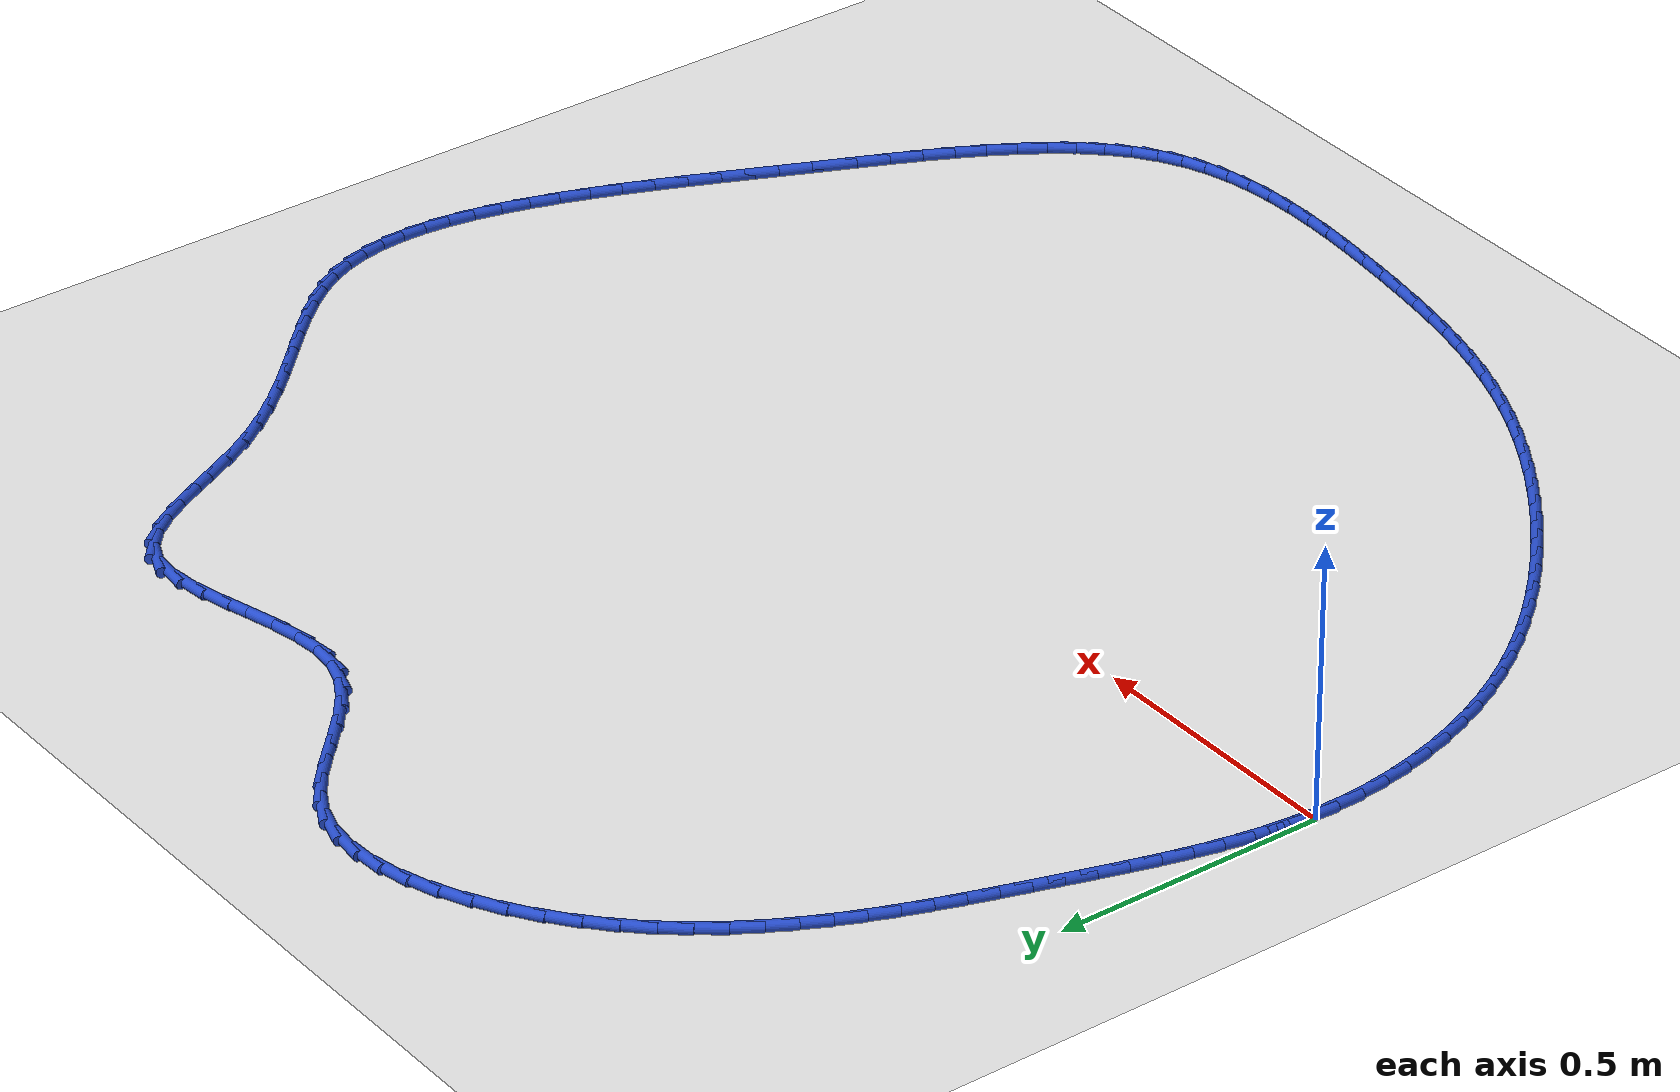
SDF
<sdf version="1.6">
 <world name="default">
  <light name="sun" type="directional">
   <pose>0 0 10 0 -0 0</pose>
   <diffuse>0.8 0.8 0.8 1</diffuse>
   <specular>0.2 0.2 0.2 1</specular>
   <attenuation>
    <range>1000</range>
    <constant>0.9</constant>
    <linear>0.01</linear>
    <quadratic>0.001</quadratic>
   </attenuation>
   <direction>-0.5 0.1 -0.9</direction>
  </light>
  <model name="ground_plane">
   <static>1</static>
   <link name="link">
    <collision name="collision">
     <geometry><plane><normal>0 0 1</normal><size>100 100</size></plane></geometry>
     <surface><friction><ode><mu>100</mu><mu2>50</mu2></ode></friction></surface>
    </collision>
    <visual name="visual">
     <cast_shadows>0</cast_shadows>
     <geometry><plane><normal>0 0 1</normal><size>100 100</size></plane></geometry>
     <material>
      <script><uri>file://media/materials/scripts/gazebo.material</uri><name>Gazebo/WhiteGlow</name></script>
     </material>
    </visual>
   </link>
  </model>
  <gravity>0 0 -9.8</gravity>
  <magnetic_field>6e-06 2.3e-05 -4.2e-05</magnetic_field>
  <atmosphere type="adiabatic"/>
  <physics name="default_physics" default="0" type="ode">
   <max_step_size>0.001</max_step_size>
   <real_time_factor>1</real_time_factor>
   <real_time_update_rate>1000</real_time_update_rate>
  </physics>
  <scene><ambient>0.4 0.4 0.4 1</ambient><background>0.7 0.7 0.7 1</background><shadows>1</shadows></scene>
  <spherical_coordinates>
   <surface_model>EARTH_WGS84</surface_model>
   <latitude_deg>0</latitude_deg>
   <longitude_deg>0</longitude_deg>
   <elevation>0</elevation>
   <heading_deg>0</heading_deg>
  </spherical_coordinates>
  <model name="line">
   <link name="link_0">
    <pose>2.42861286636753e-17 1.249000902703301e-16 0.01 0 1.57 1.502286264619102</pose>
    <collision name="collision">
     <geometry><cylinder><radius>0.01</radius><length>0.08</length></cylinder></geometry>
    </collision>
    <visual name="visual">
     <material>
      <script><name>Gazebo/Blue</name><uri>file://media/materials/scripts/gazebo.material</uri></script>
     </material>
     <geometry><cylinder><radius>0.01</radius><length>0.08</length></cylinder></geometry>
    </visual>
   </link>
   <link name="link_1">
    <pose>0.0035729545520218997 0.05207063967237306 0.01 0 1.57 1.4427990374859403</pose>
    <collision name="collision">
     <geometry><cylinder><radius>0.01</radius><length>0.08</length></cylinder></geometry>
    </collision>
    <visual name="visual">
     <material>
      <script><name>Gazebo/Blue</name><uri>file://media/materials/scripts/gazebo.material</uri></script>
     </material>
     <geometry><cylinder><radius>0.01</radius><length>0.08</length></cylinder></geometry>
    </visual>
   </link>
   <link name="link_2">
    <pose>0.010229735788563515 0.10379351710880236 0.01 0 1.57 1.3916028461294085</pose>
    <collision name="collision">
     <geometry><cylinder><radius>0.01</radius><length>0.08</length></cylinder></geometry>
    </collision>
    <visual name="visual">
     <material>
      <script><name>Gazebo/Blue</name><uri>file://media/materials/scripts/gazebo.material</uri></script>
     </material>
     <geometry><cylinder><radius>0.01</radius><length>0.08</length></cylinder></geometry>
    </visual>
   </link>
   <link name="link_3">
    <pose>0.01954264943447804 0.15520732642693813 0.01 0 1.57 1.3488477445646985</pose>
    <collision name="collision">
     <geometry><cylinder><radius>0.01</radius><length>0.08</length></cylinder></geometry>
    </collision>
    <visual name="visual">
     <material>
      <script><name>Gazebo/Blue</name><uri>file://media/materials/scripts/gazebo.material</uri></script>
     </material>
     <geometry><cylinder><radius>0.01</radius><length>0.08</length></cylinder></geometry>
    </visual>
   </link>
   <link name="link_4">
    <pose>0.031084001214618663 0.20635076174443048 0.01 0 1.57 1.3144967172494701</pose>
    <collision name="collision">
     <geometry><cylinder><radius>0.01</radius><length>0.08</length></cylinder></geometry>
    </collision>
    <visual name="visual">
     <material>
      <script><name>Gazebo/Blue</name><uri>file://media/materials/scripts/gazebo.material</uri></script>
     </material>
     <geometry><cylinder><radius>0.01</radius><length>0.08</length></cylinder></geometry>
    </visual>
   </link>
   <link name="link_5">
    <pose>0.04442609685383854 0.2572625171789295 0.01 0 1.57 1.288417019254447</pose>
    <collision name="collision">
     <geometry><cylinder><radius>0.01</radius><length>0.08</length></cylinder></geometry>
    </collision>
    <visual name="visual">
     <material>
      <script><name>Gazebo/Blue</name><uri>file://media/materials/scripts/gazebo.material</uri></script>
     </material>
     <geometry><cylinder><radius>0.01</radius><length>0.08</length></cylinder></geometry>
    </visual>
   </link>
   <link name="link_6">
    <pose>0.05914124207699089 0.30798128684808523 0.01 0 1.57 1.270452076002687</pose>
    <collision name="collision">
     <geometry><cylinder><radius>0.01</radius><length>0.08</length></cylinder></geometry>
    </collision>
    <visual name="visual">
     <material>
      <script><name>Gazebo/Blue</name><uri>file://media/materials/scripts/gazebo.material</uri></script>
     </material>
     <geometry><cylinder><radius>0.01</radius><length>0.08</length></cylinder></geometry>
    </visual>
   </link>
   <link name="link_7">
    <pose>0.07480174260892881 0.3585457648695478 0.01 0 1.57 1.26047281146192</pose>
    <collision name="collision">
     <geometry><cylinder><radius>0.01</radius><length>0.08</length></cylinder></geometry>
    </collision>
    <visual name="visual">
     <material>
      <script><name>Gazebo/Blue</name><uri>file://media/materials/scripts/gazebo.material</uri></script>
     </material>
     <geometry><cylinder><radius>0.01</radius><length>0.08</length></cylinder></geometry>
    </visual>
   </link>
   <link name="link_8">
    <pose>0.09097990417450555 0.4089946453609672 0.01 0 1.57 1.2581078427274297</pose>
    <collision name="collision">
     <geometry><cylinder><radius>0.01</radius><length>0.08</length></cylinder></geometry>
    </collision>
    <visual name="visual">
     <material>
      <script><name>Gazebo/Blue</name><uri>file://media/materials/scripts/gazebo.material</uri></script>
     </material>
     <geometry><cylinder><radius>0.01</radius><length>0.08</length></cylinder></geometry>
    </visual>
   </link>
   <link name="link_9">
    <pose>0.10726375738983393 0.4593631404900979 0.01 0 1.57 1.2565748195071877</pose>
    <collision name="collision">
     <geometry><cylinder><radius>0.01</radius><length>0.08</length></cylinder></geometry>
    </collision>
    <visual name="visual">
     <material>
      <script><name>Gazebo/Blue</name><uri>file://media/materials/scripts/gazebo.material</uri></script>
     </material>
     <geometry><cylinder><radius>0.01</radius><length>0.08</length></cylinder></geometry>
    </visual>
   </link>
   <link name="link_10">
    <pose>0.12359295539463723 0.5096086029349738 0.01 0 1.57 1.2491787727624224</pose>
    <collision name="collision">
     <geometry><cylinder><radius>0.01</radius><length>0.08</length></cylinder></geometry>
    </collision>
    <visual name="visual">
     <material>
      <script><name>Gazebo/Blue</name><uri>file://media/materials/scripts/gazebo.material</uri></script>
     </material>
     <geometry><cylinder><radius>0.01</radius><length>0.08</length></cylinder></geometry>
    </visual>
   </link>
   <link name="link_11">
    <pose>0.14025327953296127 0.5596117424865639 0.01 0 1.57 1.2355857287433745</pose>
    <collision name="collision">
     <geometry><cylinder><radius>0.01</radius><length>0.08</length></cylinder></geometry>
    </collision>
    <visual name="visual">
     <material>
      <script><name>Gazebo/Blue</name><uri>file://media/materials/scripts/gazebo.material</uri></script>
     </material>
     <geometry><cylinder><radius>0.01</radius><length>0.08</length></cylinder></geometry>
    </visual>
   </link>
   <link name="link_12">
    <pose>0.15754513709081325 0.609250030325392 0.01 0 1.57 1.2157372158213886</pose>
    <collision name="collision">
     <geometry><cylinder><radius>0.01</radius><length>0.08</length></cylinder></geometry>
    </collision>
    <visual name="visual">
     <material>
      <script><name>Gazebo/Blue</name><uri>file://media/materials/scripts/gazebo.material</uri></script>
     </material>
     <geometry><cylinder><radius>0.01</radius><length>0.08</length></cylinder></geometry>
    </visual>
   </link>
   <link name="link_13">
    <pose>0.1757689353542005 0.6584009376319819 0.01 0 1.57 1.1895842567282633</pose>
    <collision name="collision">
     <geometry><cylinder><radius>0.01</radius><length>0.08</length></cylinder></geometry>
    </collision>
    <visual name="visual">
     <material>
      <script><name>Gazebo/Blue</name><uri>file://media/materials/scripts/gazebo.material</uri></script>
     </material>
     <geometry><cylinder><radius>0.01</radius><length>0.08</length></cylinder></geometry>
    </visual>
   </link>
   <link name="link_14">
    <pose>0.19522508160913027 0.7069419355868571 0.01 0 1.57 1.1571110114907803</pose>
    <collision name="collision">
     <geometry><cylinder><radius>0.01</radius><length>0.08</length></cylinder></geometry>
    </collision>
    <visual name="visual">
     <material>
      <script><name>Gazebo/Blue</name><uri>file://media/materials/scripts/gazebo.material</uri></script>
     </material>
     <geometry><cylinder><radius>0.01</radius><length>0.08</length></cylinder></geometry>
    </visual>
   </link>
   <link name="link_15">
    <pose>0.21621398314160983 0.7547504953705414 0.01 0 1.57 1.1183662119507802</pose>
    <collision name="collision">
     <geometry><cylinder><radius>0.01</radius><length>0.08</length></cylinder></geometry>
    </collision>
    <visual name="visual">
     <material>
      <script><name>Gazebo/Blue</name><uri>file://media/materials/scripts/gazebo.material</uri></script>
     </material>
     <geometry><cylinder><radius>0.01</radius><length>0.08</length></cylinder></geometry>
    </visual>
   </link>
   <link name="link_16">
    <pose>0.23903604723764654 0.8017040881635586 0.01 0 1.57 1.07350096493883</pose>
    <collision name="collision">
     <geometry><cylinder><radius>0.01</radius><length>0.08</length></cylinder></geometry>
    </collision>
    <visual name="visual">
     <material>
      <script><name>Gazebo/Blue</name><uri>file://media/materials/scripts/gazebo.material</uri></script>
     </material>
     <geometry><cylinder><radius>0.01</radius><length>0.08</length></cylinder></geometry>
    </visual>
   </link>
   <link name="link_17">
    <pose>0.26399168118324756 0.8476801851464322 0.01 0 1.57 1.0228093818827795</pose>
    <collision name="collision">
     <geometry><cylinder><radius>0.01</radius><length>0.08</length></cylinder></geometry>
    </collision>
    <visual name="visual">
     <material>
      <script><name>Gazebo/Blue</name><uri>file://media/materials/scripts/gazebo.material</uri></script>
     </material>
     <geometry><cylinder><radius>0.01</radius><length>0.08</length></cylinder></geometry>
    </visual>
   </link>
   <link name="link_18">
    <pose>0.29138129226442033 0.8925562574996861 0.01 0 1.57 0.9667657460764356</pose>
    <collision name="collision">
     <geometry><cylinder><radius>0.01</radius><length>0.08</length></cylinder></geometry>
    </collision>
    <visual name="visual">
     <material>
      <script><name>Gazebo/Blue</name><uri>file://media/materials/scripts/gazebo.material</uri></script>
     </material>
     <geometry><cylinder><radius>0.01</radius><length>0.08</length></cylinder></geometry>
    </visual>
   </link>
   <link name="link_19">
    <pose>0.32150528776717213 0.9362097764038444 0.01 0 1.57 0.9060493488679746</pose>
    <collision name="collision">
     <geometry><cylinder><radius>0.01</radius><length>0.08</length></cylinder></geometry>
    </collision>
    <visual name="visual">
     <material>
      <script><name>Gazebo/Blue</name><uri>file://media/materials/scripts/gazebo.material</uri></script>
     </material>
     <geometry><cylinder><radius>0.01</radius><length>0.08</length></cylinder></geometry>
    </visual>
   </link>
   <link name="link_20">
    <pose>0.35466407497751007 0.9785182130394301 0.01 0 1.57 0.8415471366857648</pose>
    <collision name="collision">
     <geometry><cylinder><radius>0.01</radius><length>0.08</length></cylinder></geometry>
    </collision>
    <visual name="visual">
     <material>
      <script><name>Gazebo/Blue</name><uri>file://media/materials/scripts/gazebo.material</uri></script>
     </material>
     <geometry><cylinder><radius>0.01</radius><length>0.08</length></cylinder></geometry>
    </visual>
   </link>
   <link name="link_21">
    <pose>0.3911580611814415 1.0193590385869669 0.01 0 1.57 0.7743265099411254</pose>
    <collision name="collision">
     <geometry><cylinder><radius>0.01</radius><length>0.08</length></cylinder></geometry>
    </collision>
    <visual name="visual">
     <material>
      <script><name>Gazebo/Blue</name><uri>file://media/materials/scripts/gazebo.material</uri></script>
     </material>
     <geometry><cylinder><radius>0.01</radius><length>0.08</length></cylinder></geometry>
    </visual>
   </link>
   <link name="link_22">
    <pose>0.4312876536649738 1.0586097242269792 0.01 0 1.57 0.7058721058696109</pose>
    <collision name="collision">
     <geometry><cylinder><radius>0.01</radius><length>0.08</length></cylinder></geometry>
    </collision>
    <visual name="visual">
     <material>
      <script><name>Gazebo/Blue</name><uri>file://media/materials/scripts/gazebo.material</uri></script>
     </material>
     <geometry><cylinder><radius>0.01</radius><length>0.08</length></cylinder></geometry>
    </visual>
   </link>
   <link name="link_23">
    <pose>0.47520745321118857 1.096045927568962 0.01 0 1.57 0.6371506141087543</pose>
    <collision name="collision">
     <geometry><cylinder><radius>0.01</radius><length>0.08</length></cylinder></geometry>
    </collision>
    <visual name="visual">
     <material>
      <script><name>Gazebo/Blue</name><uri>file://media/materials/scripts/gazebo.material</uri></script>
     </material>
     <geometry><cylinder><radius>0.01</radius><length>0.08</length></cylinder></geometry>
    </visual>
   </link>
   <link name="link_24">
    <pose>0.5223938937195223 1.1309697567524502 0.01 0 1.57 0.5656986153214777</pose>
    <collision name="collision">
     <geometry><cylinder><radius>0.01</radius><length>0.08</length></cylinder></geometry>
    </collision>
    <visual name="visual">
     <material>
      <script><name>Gazebo/Blue</name><uri>file://media/materials/scripts/gazebo.material</uri></script>
     </material>
     <geometry><cylinder><radius>0.01</radius><length>0.08</length></cylinder></geometry>
    </visual>
   </link>
   <link name="link_25">
    <pose>0.5721263911060521 1.162545746461474 0.01 0 1.57 0.4883719128299961</pose>
    <collision name="collision">
     <geometry><cylinder><radius>0.01</radius><length>0.08</length></cylinder></geometry>
    </collision>
    <visual name="visual">
     <material>
      <script><name>Gazebo/Blue</name><uri>file://media/materials/scripts/gazebo.material</uri></script>
     </material>
     <geometry><cylinder><radius>0.01</radius><length>0.08</length></cylinder></geometry>
    </visual>
   </link>
   <link name="link_26">
    <pose>0.6236843397598721 1.1899384163482296 0.01 0 1.57 0.40174490105582505</pose>
    <collision name="collision">
     <geometry><cylinder><radius>0.01</radius><length>0.08</length></cylinder></geometry>
    </collision>
    <visual name="visual">
     <material>
      <script><name>Gazebo/Blue</name><uri>file://media/materials/scripts/gazebo.material</uri></script>
     </material>
     <geometry><cylinder><radius>0.01</radius><length>0.08</length></cylinder></geometry>
    </visual>
   </link>
   <link name="link_27">
    <pose>0.6763471340700766 1.2123122860649147 0.01 0 1.57 0.3018951826435892</pose>
    <collision name="collision">
     <geometry><cylinder><radius>0.01</radius><length>0.08</length></cylinder></geometry>
    </collision>
    <visual name="visual">
     <material>
      <script><name>Gazebo/Blue</name><uri>file://media/materials/scripts/gazebo.material</uri></script>
     </material>
     <geometry><cylinder><radius>0.01</radius><length>0.08</length></cylinder></geometry>
    </visual>
   </link>
   <link name="link_28">
    <pose>0.7293941684257602 1.228831875263726 0.01 0 1.57 0.18436869491970273</pose>
    <collision name="collision">
     <geometry><cylinder><radius>0.01</radius><length>0.08</length></cylinder></geometry>
    </collision>
    <visual name="visual">
     <material>
      <script><name>Gazebo/Blue</name><uri>file://media/materials/scripts/gazebo.material</uri></script>
     </material>
     <geometry><cylinder><radius>0.01</radius><length>0.08</length></cylinder></geometry>
    </visual>
   </link>
   <link name="link_29">
    <pose>0.782104837216016 1.2386617035968588 0.01 0 1.57 0.0445865423281976</pose>
    <collision name="collision">
     <geometry><cylinder><radius>0.01</radius><length>0.08</length></cylinder></geometry>
    </collision>
    <visual name="visual">
     <material>
      <script><name>Gazebo/Blue</name><uri>file://media/materials/scripts/gazebo.material</uri></script>
     </material>
     <geometry><cylinder><radius>0.01</radius><length>0.08</length></cylinder></geometry>
    </visual>
   </link>
   <link name="link_30">
    <pose>0.8337585348299392 1.2409662907165113 0.01 0 1.57 -0.12083200679489156</pose>
    <collision name="collision">
     <geometry><cylinder><radius>0.01</radius><length>0.08</length></cylinder></geometry>
    </collision>
    <visual name="visual">
     <material>
      <script><name>Gazebo/Blue</name><uri>file://media/materials/scripts/gazebo.material</uri></script>
     </material>
     <geometry><cylinder><radius>0.01</radius><length>0.08</length></cylinder></geometry>
    </visual>
   </link>
   <link name="link_31">
    <pose>0.8836346556566232 1.2349101562748794 0.01 0 1.57 -0.3114518587860264</pose>
    <collision name="collision">
     <geometry><cylinder><radius>0.01</radius><length>0.08</length></cylinder></geometry>
    </collision>
    <visual name="visual">
     <material>
      <script><name>Gazebo/Blue</name><uri>file://media/materials/scripts/gazebo.material</uri></script>
     </material>
     <geometry><cylinder><radius>0.01</radius><length>0.08</length></cylinder></geometry>
    </visual>
   </link>
   <link name="link_32">
    <pose>0.9310125940851623 1.2196578199241606 0.01 0 1.57 -0.5093944769780955</pose>
    <collision name="collision">
     <geometry><cylinder><radius>0.01</radius><length>0.08</length></cylinder></geometry>
    </collision>
    <visual name="visual">
     <material>
      <script><name>Gazebo/Blue</name><uri>file://media/materials/scripts/gazebo.material</uri></script>
     </material>
     <geometry><cylinder><radius>0.01</radius><length>0.08</length></cylinder></geometry>
    </visual>
   </link>
   <link name="link_33">
    <pose>0.9753923550490133 1.1948688829285614 0.01 0 1.57 -0.6541049799139567</pose>
    <collision name="collision">
     <geometry><cylinder><radius>0.01</radius><length>0.08</length></cylinder></geometry>
    </collision>
    <visual name="visual">
     <material>
      <script><name>Gazebo/Blue</name><uri>file://media/materials/scripts/gazebo.material</uri></script>
     </material>
     <geometry><cylinder><radius>0.01</radius><length>0.08</length></cylinder></geometry>
    </visual>
   </link>
   <link name="link_34">
    <pose>1.0173772684869675 1.1626789656555092 0.01 0 1.57 -0.7355201534508279</pose>
    <collision name="collision">
     <geometry><cylinder><radius>0.01</radius><length>0.08</length></cylinder></geometry>
    </collision>
    <visual name="visual">
     <material>
      <script><name>Gazebo/Blue</name><uri>file://media/materials/scripts/gazebo.material</uri></script>
     </material>
     <geometry><cylinder><radius>0.01</radius><length>0.08</length></cylinder></geometry>
    </visual>
   </link>
   <link name="link_35">
    <pose>1.0579148783533048 1.1259961539507097 0.01 0 1.57 -0.7627905425169553</pose>
    <collision name="collision">
     <geometry><cylinder><radius>0.01</radius><length>0.08</length></cylinder></geometry>
    </collision>
    <visual name="visual">
     <material>
      <script><name>Gazebo/Blue</name><uri>file://media/materials/scripts/gazebo.material</uri></script>
     </material>
     <geometry><cylinder><radius>0.01</radius><length>0.08</length></cylinder></geometry>
    </visual>
   </link>
   <link name="link_36">
    <pose>1.097952842314386 1.087728788846042 0.01 0 1.57 -0.7396800916671589</pose>
    <collision name="collision">
     <geometry><cylinder><radius>0.01</radius><length>0.08</length></cylinder></geometry>
    </collision>
    <visual name="visual">
     <material>
      <script><name>Gazebo/Blue</name><uri>file://media/materials/scripts/gazebo.material</uri></script>
     </material>
     <geometry><cylinder><radius>0.01</radius><length>0.08</length></cylinder></geometry>
    </visual>
   </link>
   <link name="link_37">
    <pose>1.1384388180365728 1.050785211373385 0.01 0 1.57 -0.6630756678665419</pose>
    <collision name="collision">
     <geometry><cylinder><radius>0.01</radius><length>0.08</length></cylinder></geometry>
    </collision>
    <visual name="visual">
     <material>
      <script><name>Gazebo/Blue</name><uri>file://media/materials/scripts/gazebo.material</uri></script>
     </material>
     <geometry><cylinder><radius>0.01</radius><length>0.08</length></cylinder></geometry>
    </visual>
   </link>
   <link name="link_38">
    <pose>1.1803204631862243 1.0180737625646175 0.01 0 1.57 -0.5242375365830264</pose>
    <collision name="collision">
     <geometry><cylinder><radius>0.01</radius><length>0.08</length></cylinder></geometry>
    </collision>
    <visual name="visual">
     <material>
      <script><name>Gazebo/Blue</name><uri>file://media/materials/scripts/gazebo.material</uri></script>
     </material>
     <geometry><cylinder><radius>0.01</radius><length>0.08</length></cylinder></geometry>
    </visual>
   </link>
   <link name="link_39">
    <pose>1.2245454354297027 0.992502783451618 0.01 0 1.57 -0.3157472961545364</pose>
    <collision name="collision">
     <geometry><cylinder><radius>0.01</radius><length>0.08</length></cylinder></geometry>
    </collision>
    <visual name="visual">
     <material>
      <script><name>Gazebo/Blue</name><uri>file://media/materials/scripts/gazebo.material</uri></script>
     </material>
     <geometry><cylinder><radius>0.01</radius><length>0.08</length></cylinder></geometry>
    </visual>
   </link>
   <link name="link_40">
    <pose>1.2720613380431465 0.9769804647768914 0.01 0 1.57 -0.07296806648989863</pose>
    <collision name="collision">
     <geometry><cylinder><radius>0.01</radius><length>0.08</length></cylinder></geometry>
    </collision>
    <visual name="visual">
     <material>
      <script><name>Gazebo/Blue</name><uri>file://media/materials/scripts/gazebo.material</uri></script>
     </material>
     <geometry><cylinder><radius>0.01</radius><length>0.08</length></cylinder></geometry>
    </visual>
   </link>
   <link name="link_41">
    <pose>1.323386452826087 0.9732287094854568 0.01 0 1.57 0.10461789030769843</pose>
    <collision name="collision">
     <geometry><cylinder><radius>0.01</radius><length>0.08</length></cylinder></geometry>
    </collision>
    <visual name="visual">
     <material>
      <script><name>Gazebo/Blue</name><uri>file://media/materials/scripts/gazebo.material</uri></script>
     </material>
     <geometry><cylinder><radius>0.01</radius><length>0.08</length></cylinder></geometry>
    </visual>
   </link>
   <link name="link_42">
    <pose>1.3775729698512553 0.9789183613038908 0.01 0 1.57 0.21080977844076354</pose>
    <collision name="collision">
     <geometry><cylinder><radius>0.01</radius><length>0.08</length></cylinder></geometry>
    </collision>
    <visual name="visual">
     <material>
      <script><name>Gazebo/Blue</name><uri>file://media/materials/scripts/gazebo.material</uri></script>
     </material>
     <geometry><cylinder><radius>0.01</radius><length>0.08</length></cylinder></geometry>
    </visual>
   </link>
   <link name="link_43">
    <pose>1.4333603952737892 0.9908562654492071 0.01 0 1.57 0.2610277934951713</pose>
    <collision name="collision">
     <geometry><cylinder><radius>0.01</radius><length>0.08</length></cylinder></geometry>
    </collision>
    <visual name="visual">
     <material>
      <script><name>Gazebo/Blue</name><uri>file://media/materials/scripts/gazebo.material</uri></script>
     </material>
     <geometry><cylinder><radius>0.01</radius><length>0.08</length></cylinder></geometry>
    </visual>
   </link>
   <link name="link_44">
    <pose>1.4894882352488263 1.0058492671384203 0.01 0 1.57 0.262848069948994</pose>
    <collision name="collision">
     <geometry><cylinder><radius>0.01</radius><length>0.08</length></cylinder></geometry>
    </collision>
    <visual name="visual">
     <material>
      <script><name>Gazebo/Blue</name><uri>file://media/materials/scripts/gazebo.material</uri></script>
     </material>
     <geometry><cylinder><radius>0.01</radius><length>0.08</length></cylinder></geometry>
    </visual>
   </link>
   <link name="link_45">
    <pose>1.544695995931503 1.020704211588544 0.01 0 1.57 0.21399014740650962</pose>
    <collision name="collision">
     <geometry><cylinder><radius>0.01</radius><length>0.08</length></cylinder></geometry>
    </collision>
    <visual name="visual">
     <material>
      <script><name>Gazebo/Blue</name><uri>file://media/materials/scripts/gazebo.material</uri></script>
     </material>
     <geometry><cylinder><radius>0.01</radius><length>0.08</length></cylinder></geometry>
    </visual>
   </link>
   <link name="link_46">
    <pose>1.5977231834769574 1.0322279440165931 0.01 0 1.57 0.10048232320105349</pose>
    <collision name="collision">
     <geometry><cylinder><radius>0.01</radius><length>0.08</length></cylinder></geometry>
    </collision>
    <visual name="visual">
     <material>
      <script><name>Gazebo/Blue</name><uri>file://media/materials/scripts/gazebo.material</uri></script>
     </material>
     <geometry><cylinder><radius>0.01</radius><length>0.08</length></cylinder></geometry>
    </visual>
   </link>
   <link name="link_47">
    <pose>1.647309304040325 1.0372273096395808 0.01 0 1.57 -0.10473294667288804</pose>
    <collision name="collision">
     <geometry><cylinder><radius>0.01</radius><length>0.08</length></cylinder></geometry>
    </collision>
    <visual name="visual">
     <material>
      <script><name>Gazebo/Blue</name><uri>file://media/materials/scripts/gazebo.material</uri></script>
     </material>
     <geometry><cylinder><radius>0.01</radius><length>0.08</length></cylinder></geometry>
    </visual>
   </link>
   <link name="link_48">
    <pose>1.692193863776745 1.0325091536745217 0.01 0 1.57 -0.41792675565798343</pose>
    <collision name="collision">
     <geometry><cylinder><radius>0.01</radius><length>0.08</length></cylinder></geometry>
    </collision>
    <visual name="visual">
     <material>
      <script><name>Gazebo/Blue</name><uri>file://media/materials/scripts/gazebo.material</uri></script>
     </material>
     <geometry><cylinder><radius>0.01</radius><length>0.08</length></cylinder></geometry>
    </visual>
   </link>
   <link name="link_49">
    <pose>1.7312501048889741 1.0151647402972477 0.01 0 1.57 -0.7212500035879534</pose>
    <collision name="collision">
     <geometry><cylinder><radius>0.01</radius><length>0.08</length></cylinder></geometry>
    </collision>
    <visual name="visual">
     <material>
      <script><name>Gazebo/Blue</name><uri>file://media/materials/scripts/gazebo.material</uri></script>
     </material>
     <geometry><cylinder><radius>0.01</radius><length>0.08</length></cylinder></geometry>
    </visual>
   </link>
   <link name="link_50">
    <pose>1.7648993177219 0.9855775966793549 0.01 0 1.57 -0.9246587629446178</pose>
    <collision name="collision">
     <geometry><cylinder><radius>0.01</radius><length>0.08</length></cylinder></geometry>
    </collision>
    <visual name="visual">
     <material>
      <script><name>Gazebo/Blue</name><uri>file://media/materials/scripts/gazebo.material</uri></script>
     </material>
     <geometry><cylinder><radius>0.01</radius><length>0.08</length></cylinder></geometry>
    </visual>
   </link>
   <link name="link_51">
    <pose>1.7945583925531294 0.9462486110278513 0.01 0 1.57 -1.04341330971691</pose>
    <collision name="collision">
     <geometry><cylinder><radius>0.01</radius><length>0.08</length></cylinder></geometry>
    </collision>
    <visual name="visual">
     <material>
      <script><name>Gazebo/Blue</name><uri>file://media/materials/scripts/gazebo.material</uri></script>
     </material>
     <geometry><cylinder><radius>0.01</radius><length>0.08</length></cylinder></geometry>
    </visual>
   </link>
   <link name="link_52">
    <pose>1.8216606724528261 0.8997136620120122 0.01 0 1.57 -1.1012867330618223</pose>
    <collision name="collision">
     <geometry><cylinder><radius>0.01</radius><length>0.08</length></cylinder></geometry>
    </collision>
    <visual name="visual">
     <material>
      <script><name>Gazebo/Blue</name><uri>file://media/materials/scripts/gazebo.material</uri></script>
     </material>
     <geometry><cylinder><radius>0.01</radius><length>0.08</length></cylinder></geometry>
    </visual>
   </link>
   <link name="link_53">
    <pose>1.847639500491152 0.8485086283011136 0.01 0 1.57 -1.112877896980893</pose>
    <collision name="collision">
     <geometry><cylinder><radius>0.01</radius><length>0.08</length></cylinder></geometry>
    </collision>
    <visual name="visual">
     <material>
      <script><name>Gazebo/Blue</name><uri>file://media/materials/scripts/gazebo.material</uri></script>
     </material>
     <geometry><cylinder><radius>0.01</radius><length>0.08</length></cylinder></geometry>
    </visual>
   </link>
   <link name="link_54">
    <pose>1.8739282197382698 0.7951693885644302 0.01 0 1.57 -1.083805874959155</pose>
    <collision name="collision">
     <geometry><cylinder><radius>0.01</radius><length>0.08</length></cylinder></geometry>
    </collision>
    <visual name="visual">
     <material>
      <script><name>Gazebo/Blue</name><uri>file://media/materials/scripts/gazebo.material</uri></script>
     </material>
     <geometry><cylinder><radius>0.01</radius><length>0.08</length></cylinder></geometry>
    </visual>
   </link>
   <link name="link_55">
    <pose>1.901960173264342 0.742231821471237 0.01 0 1.57 -1.0152717243889782</pose>
    <collision name="collision">
     <geometry><cylinder><radius>0.01</radius><length>0.08</length></cylinder></geometry>
    </collision>
    <visual name="visual">
     <material>
      <script><name>Gazebo/Blue</name><uri>file://media/materials/scripts/gazebo.material</uri></script>
     </material>
     <geometry><cylinder><radius>0.01</radius><length>0.08</length></cylinder></geometry>
    </visual>
   </link>
   <link name="link_56">
    <pose>1.9330748572564969 0.6921060615678157 0.01 0 1.57 -0.9367641811042429</pose>
    <collision name="collision">
     <geometry><cylinder><radius>0.01</radius><length>0.08</length></cylinder></geometry>
    </collision>
    <visual name="visual">
     <material>
      <script><name>Gazebo/Blue</name><uri>file://media/materials/scripts/gazebo.material</uri></script>
     </material>
     <geometry><cylinder><radius>0.01</radius><length>0.08</length></cylinder></geometry>
    </visual>
   </link>
   <link name="link_57">
    <pose>1.9673430254851392 0.6455022732220153 0.01 0 1.57 -0.8726429496231685</pose>
    <collision name="collision">
     <geometry><cylinder><radius>0.01</radius><length>0.08</length></cylinder></geometry>
    </collision>
    <visual name="visual">
     <material>
      <script><name>Gazebo/Blue</name><uri>file://media/materials/scripts/gazebo.material</uri></script>
     </material>
     <geometry><cylinder><radius>0.01</radius><length>0.08</length></cylinder></geometry>
    </visual>
   </link>
   <link name="link_58">
    <pose>2.00392371492149 0.6019090242432694 0.01 0 1.57 -0.824399737058991</pose>
    <collision name="collision">
     <geometry><cylinder><radius>0.01</radius><length>0.08</length></cylinder></geometry>
    </collision>
    <visual name="visual">
     <material>
      <script><name>Gazebo/Blue</name><uri>file://media/materials/scripts/gazebo.material</uri></script>
     </material>
     <geometry><cylinder><radius>0.01</radius><length>0.08</length></cylinder></geometry>
    </visual>
   </link>
   <link name="link_59">
    <pose>2.041955974059701 0.5607881001607921 0.01 0 1.57 -0.7926456725663542</pose>
    <collision name="collision">
     <geometry><cylinder><radius>0.01</radius><length>0.08</length></cylinder></geometry>
    </collision>
    <visual name="visual">
     <material>
      <script><name>Gazebo/Blue</name><uri>file://media/materials/scripts/gazebo.material</uri></script>
     </material>
     <geometry><cylinder><radius>0.01</radius><length>0.08</length></cylinder></geometry>
    </visual>
   </link>
   <link name="link_60">
    <pose>2.080578851393925 0.5216012865037986 0.01 0 1.57 -0.7780224002680669</pose>
    <collision name="collision">
     <geometry><cylinder><radius>0.01</radius><length>0.08</length></cylinder></geometry>
    </collision>
    <visual name="visual">
     <material>
      <script><name>Gazebo/Blue</name><uri>file://media/materials/scripts/gazebo.material</uri></script>
     </material>
     <geometry><cylinder><radius>0.01</radius><length>0.08</length></cylinder></geometry>
    </visual>
   </link>
   <link name="link_61">
    <pose>2.118931395418314 0.4838103688015034 0.01 0 1.57 -0.7815140894746363</pose>
    <collision name="collision">
     <geometry><cylinder><radius>0.01</radius><length>0.08</length></cylinder></geometry>
    </collision>
    <visual name="visual">
     <material>
      <script><name>Gazebo/Blue</name><uri>file://media/materials/scripts/gazebo.material</uri></script>
     </material>
     <geometry><cylinder><radius>0.01</radius><length>0.08</length></cylinder></geometry>
    </visual>
   </link>
   <link name="link_62">
    <pose>2.1561526546270193 0.4468771325831217 0.01 0 1.57 -0.8046704499025903</pose>
    <collision name="collision">
     <geometry><cylinder><radius>0.01</radius><length>0.08</length></cylinder></geometry>
    </collision>
    <visual name="visual">
     <material>
      <script><name>Gazebo/Blue</name><uri>file://media/materials/scripts/gazebo.material</uri></script>
     </material>
     <geometry><cylinder><radius>0.01</radius><length>0.08</length></cylinder></geometry>
    </visual>
   </link>
   <link name="link_63">
    <pose>2.1913816775141934 0.41026336337786773 0.01 0 1.57 -0.8497045158711476</pose>
    <collision name="collision">
     <geometry><cylinder><radius>0.01</radius><length>0.08</length></cylinder></geometry>
    </collision>
    <visual name="visual">
     <material>
      <script><name>Gazebo/Blue</name><uri>file://media/materials/scripts/gazebo.material</uri></script>
     </material>
     <geometry><cylinder><radius>0.01</radius><length>0.08</length></cylinder></geometry>
    </visual>
   </link>
   <link name="link_64">
    <pose>2.2237575125739886 0.3734308467149567 0.01 0 1.57 -0.9193478382451928</pose>
    <collision name="collision">
     <geometry><cylinder><radius>0.01</radius><length>0.08</length></cylinder></geometry>
    </collision>
    <visual name="visual">
     <material>
      <script><name>Gazebo/Blue</name><uri>file://media/materials/scripts/gazebo.material</uri></script>
     </material>
     <geometry><cylinder><radius>0.01</radius><length>0.08</length></cylinder></geometry>
    </visual>
   </link>
   <link name="link_65">
    <pose>2.2524192083005574 0.3358413681236032 0.01 0 1.57 -1.0162071746384247</pose>
    <collision name="collision">
     <geometry><cylinder><radius>0.01</radius><length>0.08</length></cylinder></geometry>
    </collision>
    <visual name="visual">
     <material>
      <script><name>Gazebo/Blue</name><uri>file://media/materials/scripts/gazebo.material</uri></script>
     </material>
     <geometry><cylinder><radius>0.01</radius><length>0.08</length></cylinder></geometry>
    </visual>
   </link>
   <link name="link_66">
    <pose>2.2765058131880513 0.29695671313302185 0.01 0 1.57 -1.1399993831500304</pose>
    <collision name="collision">
     <geometry><cylinder><radius>0.01</radius><length>0.08</length></cylinder></geometry>
    </collision>
    <visual name="visual">
     <material>
      <script><name>Gazebo/Blue</name><uri>file://media/materials/scripts/gazebo.material</uri></script>
     </material>
     <geometry><cylinder><radius>0.01</radius><length>0.08</length></cylinder></geometry>
    </visual>
   </link>
   <link name="link_67">
    <pose>2.2952065788993368 0.25626624823606614 0.01 0 1.57 -1.2708781172042392</pose>
    <collision name="collision">
     <geometry><cylinder><radius>0.01</radius><length>0.08</length></cylinder></geometry>
    </collision>
    <visual name="visual">
     <material>
      <script><name>Gazebo/Blue</name><uri>file://media/materials/scripts/gazebo.material</uri></script>
     </material>
     <geometry><cylinder><radius>0.01</radius><length>0.08</length></cylinder></geometry>
    </visual>
   </link>
   <link name="link_68">
    <pose>2.3083907863001993 0.21363293906681668 0.01 0 1.57 -1.392130911115739</pose>
    <collision name="collision">
     <geometry><cylinder><radius>0.01</radius><length>0.08</length></cylinder></geometry>
    </collision>
    <visual name="visual">
     <material>
      <script><name>Gazebo/Blue</name><uri>file://media/materials/scripts/gazebo.material</uri></script>
     </material>
     <geometry><cylinder><radius>0.01</radius><length>0.08</length></cylinder></geometry>
    </visual>
   </link>
   <link name="link_69">
    <pose>2.316417041386933 0.16918858007987508 0.01 0 1.57 -1.500706799169652</pose>
    <collision name="collision">
     <geometry><cylinder><radius>0.01</radius><length>0.08</length></cylinder></geometry>
    </collision>
    <visual name="visual">
     <material>
      <script><name>Gazebo/Blue</name><uri>file://media/materials/scripts/gazebo.material</uri></script>
     </material>
     <geometry><cylinder><radius>0.01</radius><length>0.08</length></cylinder></geometry>
    </visual>
   </link>
   <link name="link_70">
    <pose>2.3196547127702085 0.12307087856927765 0.01 0 1.57 1.5460068418699018</pose>
    <collision name="collision">
     <geometry><cylinder><radius>0.01</radius><length>0.08</length></cylinder></geometry>
    </collision>
    <visual name="visual">
     <material>
      <script><name>Gazebo/Blue</name><uri>file://media/materials/scripts/gazebo.material</uri></script>
     </material>
     <geometry><cylinder><radius>0.01</radius><length>0.08</length></cylinder></geometry>
    </visual>
   </link>
   <link name="link_71">
    <pose>2.318473169060698 0.0754175418290622 0.01 0 1.57 1.4645464753518946</pose>
    <collision name="collision">
     <geometry><cylinder><radius>0.01</radius><length>0.08</length></cylinder></geometry>
    </collision>
    <visual name="visual">
     <material>
      <script><name>Gazebo/Blue</name><uri>file://media/materials/scripts/gazebo.material</uri></script>
     </material>
     <geometry><cylinder><radius>0.01</radius><length>0.08</length></cylinder></geometry>
    </visual>
   </link>
   <link name="link_72">
    <pose>2.3132417788690716 0.02636627715326527 0.01 0 1.57 1.3954809518263236</pose>
    <collision name="collision">
     <geometry><cylinder><radius>0.01</radius><length>0.08</length></cylinder></geometry>
    </collision>
    <visual name="visual">
     <material>
      <script><name>Gazebo/Blue</name><uri>file://media/materials/scripts/gazebo.material</uri></script>
     </material>
     <geometry><cylinder><radius>0.01</radius><length>0.08</length></cylinder></geometry>
    </visual>
   </link>
   <link name="link_73">
    <pose>2.3043299108060014 -0.023945208164076956 0.01 0 1.57 1.3374802903065772</pose>
    <collision name="collision">
     <geometry><cylinder><radius>0.01</radius><length>0.08</length></cylinder></geometry>
    </collision>
    <visual name="visual">
     <material>
      <script><name>Gazebo/Blue</name><uri>file://media/materials/scripts/gazebo.material</uri></script>
     </material>
     <geometry><cylinder><radius>0.01</radius><length>0.08</length></cylinder></geometry>
    </visual>
   </link>
   <link name="link_74">
    <pose>2.2921069334821587 -0.0753792068289258 0.01 0 1.57 1.2891854659725064</pose>
    <collision name="collision">
     <geometry><cylinder><radius>0.01</radius><length>0.08</length></cylinder></geometry>
    </collision>
    <visual name="visual">
     <material>
      <script><name>Gazebo/Blue</name><uri>file://media/materials/scripts/gazebo.material</uri></script>
     </material>
     <geometry><cylinder><radius>0.01</radius><length>0.08</length></cylinder></geometry>
    </visual>
   </link>
   <link name="link_75">
    <pose>2.2769422155082153 -0.12779801154724507 0.01 0 1.57 1.2493535060694492</pose>
    <collision name="collision">
     <geometry><cylinder><radius>0.01</radius><length>0.08</length></cylinder></geometry>
    </collision>
    <visual name="visual">
     <material>
      <script><name>Gazebo/Blue</name><uri>file://media/materials/scripts/gazebo.material</uri></script>
     </material>
     <geometry><cylinder><radius>0.01</radius><length>0.08</length></cylinder></geometry>
    </visual>
   </link>
   <link name="link_76">
    <pose>2.2592051254948413 -0.18106391502499786 0.01 0 1.57 1.2169178602378736</pose>
    <collision name="collision">
     <geometry><cylinder><radius>0.01</radius><length>0.08</length></cylinder></geometry>
    </collision>
    <visual name="visual">
     <material>
      <script><name>Gazebo/Blue</name><uri>file://media/materials/scripts/gazebo.material</uri></script>
     </material>
     <geometry><cylinder><radius>0.01</radius><length>0.08</length></cylinder></geometry>
    </visual>
   </link>
   <link name="link_77">
    <pose>2.2392650320527085 -0.23503920996814717 0.01 0 1.57 1.1910023412791821</pose>
    <collision name="collision">
     <geometry><cylinder><radius>0.01</radius><length>0.08</length></cylinder></geometry>
    </collision>
    <visual name="visual">
     <material>
      <script><name>Gazebo/Blue</name><uri>file://media/materials/scripts/gazebo.material</uri></script>
     </material>
     <geometry><cylinder><radius>0.01</radius><length>0.08</length></cylinder></geometry>
    </visual>
   </link>
   <link name="link_78">
    <pose>2.217491303792488 -0.28958618908265676 0.01 0 1.57 1.1709133052564993</pose>
    <collision name="collision">
     <geometry><cylinder><radius>0.01</radius><length>0.08</length></cylinder></geometry>
    </collision>
    <visual name="visual">
     <material>
      <script><name>Gazebo/Blue</name><uri>file://media/materials/scripts/gazebo.material</uri></script>
     </material>
     <geometry><cylinder><radius>0.01</radius><length>0.08</length></cylinder></geometry>
    </visual>
   </link>
   <link name="link_79">
    <pose>2.1942533093248504 -0.34456714507448793 0.01 0 1.57 1.1561240657351564</pose>
    <collision name="collision">
     <geometry><cylinder><radius>0.01</radius><length>0.08</length></cylinder></geometry>
    </collision>
    <visual name="visual">
     <material>
      <script><name>Gazebo/Blue</name><uri>file://media/materials/scripts/gazebo.material</uri></script>
     </material>
     <geometry><cylinder><radius>0.01</radius><length>0.08</length></cylinder></geometry>
    </visual>
   </link>
   <link name="link_80">
    <pose>2.169920417260469 -0.39984437064960454 0.01 0 1.57 1.1462588013819728</pose>
    <collision name="collision">
     <geometry><cylinder><radius>0.01</radius><length>0.08</length></cylinder></geometry>
    </collision>
    <visual name="visual">
     <material>
      <script><name>Gazebo/Blue</name><uri>file://media/materials/scripts/gazebo.material</uri></script>
     </material>
     <geometry><cylinder><radius>0.01</radius><length>0.08</length></cylinder></geometry>
    </visual>
   </link>
   <link name="link_81">
    <pose>2.1448619962100133 -0.45528015851396975 0.01 0 1.57 1.1410794474713768</pose>
    <collision name="collision">
     <geometry><cylinder><radius>0.01</radius><length>0.08</length></cylinder></geometry>
    </collision>
    <visual name="visual">
     <material>
      <script><name>Gazebo/Blue</name><uri>file://media/materials/scripts/gazebo.material</uri></script>
     </material>
     <geometry><cylinder><radius>0.01</radius><length>0.08</length></cylinder></geometry>
    </visual>
   </link>
   <link name="link_82">
    <pose>2.119447414784155 -0.5107368013735474 0.01 0 1.57 1.1404771448761992</pose>
    <collision name="collision">
     <geometry><cylinder><radius>0.01</radius><length>0.08</length></cylinder></geometry>
    </collision>
    <visual name="visual">
     <material>
      <script><name>Gazebo/Blue</name><uri>file://media/materials/scripts/gazebo.material</uri></script>
     </material>
     <geometry><cylinder><radius>0.01</radius><length>0.08</length></cylinder></geometry>
    </visual>
   </link>
   <link name="link_83">
    <pose>2.094046041593566 -0.5660765919342985 0.01 0 1.57 1.1437506375032513</pose>
    <collision name="collision">
     <geometry><cylinder><radius>0.01</radius><length>0.08</length></cylinder></geometry>
    </collision>
    <visual name="visual">
     <material>
      <script><name>Gazebo/Blue</name><uri>file://media/materials/scripts/gazebo.material</uri></script>
     </material>
     <geometry><cylinder><radius>0.01</radius><length>0.08</length></cylinder></geometry>
    </visual>
   </link>
   <link name="link_84">
    <pose>2.068986537868381 -0.6211463544181676 0.01 0 1.57 1.1438352347236482</pose>
    <collision name="collision">
     <geometry><cylinder><radius>0.01</radius><length>0.08</length></cylinder></geometry>
    </collision>
    <visual name="visual">
     <material>
      <script><name>Gazebo/Blue</name><uri>file://media/materials/scripts/gazebo.material</uri></script>
     </material>
     <geometry><cylinder><radius>0.01</radius><length>0.08</length></cylinder></geometry>
    </visual>
   </link>
   <link name="link_85">
    <pose>2.0441948185654875 -0.6756398726350197 0.01 0 1.57 1.1364705656015068</pose>
    <collision name="collision">
     <geometry><cylinder><radius>0.01</radius><length>0.08</length></cylinder></geometry>
    </collision>
    <visual name="visual">
     <material>
      <script><name>Gazebo/Blue</name><uri>file://media/materials/scripts/gazebo.material</uri></script>
     </material>
     <geometry><cylinder><radius>0.01</radius><length>0.08</length></cylinder></geometry>
    </visual>
   </link>
   <link name="link_86">
    <pose>2.019366931641542 -0.7291635827449101 0.01 0 1.57 1.1211870631974363</pose>
    <collision name="collision">
     <geometry><cylinder><radius>0.01</radius><length>0.08</length></cylinder></geometry>
    </collision>
    <visual name="visual">
     <material>
      <script><name>Gazebo/Blue</name><uri>file://media/materials/scripts/gazebo.material</uri></script>
     </material>
     <geometry><cylinder><radius>0.01</radius><length>0.08</length></cylinder></geometry>
    </visual>
   </link>
   <link name="link_87">
    <pose>1.9941962403137101 -0.7813229007280312 0.01 0 1.57 1.0973566188363908</pose>
    <collision name="collision">
     <geometry><cylinder><radius>0.01</radius><length>0.08</length></cylinder></geometry>
    </collision>
    <visual name="visual">
     <material>
      <script><name>Gazebo/Blue</name><uri>file://media/materials/scripts/gazebo.material</uri></script>
     </material>
     <geometry><cylinder><radius>0.01</radius><length>0.08</length></cylinder></geometry>
    </visual>
   </link>
   <link name="link_88">
    <pose>1.9683761077991582 -0.8317232425645725 0.01 0 1.57 1.064134388265504</pose>
    <collision name="collision">
     <geometry><cylinder><radius>0.01</radius><length>0.08</length></cylinder></geometry>
    </collision>
    <visual name="visual">
     <material>
      <script><name>Gazebo/Blue</name><uri>file://media/materials/scripts/gazebo.material</uri></script>
     </material>
     <geometry><cylinder><radius>0.01</radius><length>0.08</length></cylinder></geometry>
    </visual>
   </link>
   <link name="link_89">
    <pose>1.941599897315051 -0.8799700242347265 0.01 0 1.57 1.0204647552105088</pose>
    <collision name="collision">
     <geometry><cylinder><radius>0.01</radius><length>0.08</length></cylinder></geometry>
    </collision>
    <visual name="visual">
     <material>
      <script><name>Gazebo/Blue</name><uri>file://media/materials/scripts/gazebo.material</uri></script>
     </material>
     <geometry><cylinder><radius>0.01</radius><length>0.08</length></cylinder></geometry>
    </visual>
   </link>
   <link name="link_90">
    <pose>1.913560972078554 -0.925668661718684 0.01 0 1.57 0.9651246847590658</pose>
    <collision name="collision">
     <geometry><cylinder><radius>0.01</radius><length>0.08</length></cylinder></geometry>
    </collision>
    <visual name="visual">
     <material>
      <script><name>Gazebo/Blue</name><uri>file://media/materials/scripts/gazebo.material</uri></script>
     </material>
     <geometry><cylinder><radius>0.01</radius><length>0.08</length></cylinder></geometry>
    </visual>
   </link>
   <link name="link_91">
    <pose>1.8839526953068322 -0.968424570996638 0.01 0 1.57 0.8968387875746343</pose>
    <collision name="collision">
     <geometry><cylinder><radius>0.01</radius><length>0.08</length></cylinder></geometry>
    </collision>
    <visual name="visual">
     <material>
      <script><name>Gazebo/Blue</name><uri>file://media/materials/scripts/gazebo.material</uri></script>
     </material>
     <geometry><cylinder><radius>0.01</radius><length>0.08</length></cylinder></geometry>
    </visual>
   </link>
   <link name="link_92">
    <pose>1.8524684302170527 -1.0078431680487778 0.01 0 1.57 0.814513308395862</pose>
    <collision name="collision">
     <geometry><cylinder><radius>0.01</radius><length>0.08</length></cylinder></geometry>
    </collision>
    <visual name="visual">
     <material>
      <script><name>Gazebo/Blue</name><uri>file://media/materials/scripts/gazebo.material</uri></script>
     </material>
     <geometry><cylinder><radius>0.01</radius><length>0.08</length></cylinder></geometry>
    </visual>
   </link>
   <link name="link_93">
    <pose>1.8188015400263784 -1.0435298688552954 0.01 0 1.57 0.7176317735627801</pose>
    <collision name="collision">
     <geometry><cylinder><radius>0.01</radius><length>0.08</length></cylinder></geometry>
    </collision>
    <visual name="visual">
     <material>
      <script><name>Gazebo/Blue</name><uri>file://media/materials/scripts/gazebo.material</uri></script>
     </material>
     <geometry><cylinder><radius>0.01</radius><length>0.08</length></cylinder></geometry>
    </visual>
   </link>
   <link name="link_94">
    <pose>1.782645387951977 -1.075090089396383 0.01 0 1.57 0.6067992156913515</pose>
    <collision name="collision">
     <geometry><cylinder><radius>0.01</radius><length>0.08</length></cylinder></geometry>
    </collision>
    <visual name="visual">
     <material>
      <script><name>Gazebo/Blue</name><uri>file://media/materials/scripts/gazebo.material</uri></script>
     </material>
     <geometry><cylinder><radius>0.01</radius><length>0.08</length></cylinder></geometry>
    </visual>
   </link>
   <link name="link_95">
    <pose>1.7436933372110122 -1.1021292456522316 0.01 0 1.57 0.4842849290200689</pose>
    <collision name="collision">
     <geometry><cylinder><radius>0.01</radius><length>0.08</length></cylinder></geometry>
    </collision>
    <visual name="visual">
     <material>
      <script><name>Gazebo/Blue</name><uri>file://media/materials/scripts/gazebo.material</uri></script>
     </material>
     <geometry><cylinder><radius>0.01</radius><length>0.08</length></cylinder></geometry>
    </visual>
   </link>
   <link name="link_96">
    <pose>1.7016388225276926 -1.124252836935228 0.01 0 1.57 0.3591166905997008</pose>
    <collision name="collision">
     <geometry><cylinder><radius>0.01</radius><length>0.08</length></cylinder></geometry>
    </collision>
    <visual name="visual">
     <material>
      <script><name>Gazebo/Blue</name><uri>file://media/materials/scripts/gazebo.material</uri></script>
     </material>
     <geometry><cylinder><radius>0.01</radius><length>0.08</length></cylinder></geometry>
    </visual>
   </link>
   <link name="link_97">
    <pose>1.6563396444833514 -1.141257909676891 0.01 0 1.57 0.2496820367132497</pose>
    <collision name="collision">
     <geometry><cylinder><radius>0.01</radius><length>0.08</length></cylinder></geometry>
    </collision>
    <visual name="visual">
     <material>
      <script><name>Gazebo/Blue</name><uri>file://media/materials/scripts/gazebo.material</uri></script>
     </material>
     <geometry><cylinder><radius>0.01</radius><length>0.08</length></cylinder></geometry>
    </visual>
   </link>
   <link name="link_98">
    <pose>1.6081686077029633 -1.1535416808223988 0.01 0 1.57 0.15838147728008006</pose>
    <collision name="collision">
     <geometry><cylinder><radius>0.01</radius><length>0.08</length></cylinder></geometry>
    </collision>
    <visual name="visual">
     <material>
      <script><name>Gazebo/Blue</name><uri>file://media/materials/scripts/gazebo.material</uri></script>
     </material>
     <geometry><cylinder><radius>0.01</radius><length>0.08</length></cylinder></geometry>
    </visual>
   </link>
   <link name="link_99">
    <pose>1.5575991143959245 -1.161618600772979 0.01 0 1.57 0.08332991020287756</pose>
    <collision name="collision">
     <geometry><cylinder><radius>0.01</radius><length>0.08</length></cylinder></geometry>
    </collision>
    <visual name="visual">
     <material>
      <script><name>Gazebo/Blue</name><uri>file://media/materials/scripts/gazebo.material</uri></script>
     </material>
     <geometry><cylinder><radius>0.01</radius><length>0.08</length></cylinder></geometry>
    </visual>
   </link>
   <link name="link_100">
    <pose>1.5051045667716298 -1.1660031199298584 0.01 0 1.57 0.02236242103384555</pose>
    <collision name="collision">
     <geometry><cylinder><radius>0.01</radius><length>0.08</length></cylinder></geometry>
    </collision>
    <visual name="visual">
     <material>
      <script><name>Gazebo/Blue</name><uri>file://media/materials/scripts/gazebo.material</uri></script>
     </material>
     <geometry><cylinder><radius>0.01</radius><length>0.08</length></cylinder></geometry>
    </visual>
   </link>
   <link name="link_101">
    <pose>1.4511583670394768 -1.1672096886942647 0.01 0 1.57 -0.026519877131066245</pose>
    <collision name="collision">
     <geometry><cylinder><radius>0.01</radius><length>0.08</length></cylinder></geometry>
    </collision>
    <visual name="visual">
     <material>
      <script><name>Gazebo/Blue</name><uri>file://media/materials/scripts/gazebo.material</uri></script>
     </material>
     <geometry><cylinder><radius>0.01</radius><length>0.08</length></cylinder></geometry>
    </visual>
   </link>
   <link name="link_102">
    <pose>1.3962339174088603 -1.165752757467424 0.01 0 1.57 -0.06496395895952128</pose>
    <collision name="collision">
     <geometry><cylinder><radius>0.01</radius><length>0.08</length></cylinder></geometry>
    </collision>
    <visual name="visual">
     <material>
      <script><name>Gazebo/Blue</name><uri>file://media/materials/scripts/gazebo.material</uri></script>
     </material>
     <geometry><cylinder><radius>0.01</radius><length>0.08</length></cylinder></geometry>
    </visual>
   </link>
   <link name="link_103">
    <pose>1.3408046200891761 -1.1621467766505644 0.01 0 1.57 -0.09421197071604645</pose>
    <collision name="collision">
     <geometry><cylinder><radius>0.01</radius><length>0.08</length></cylinder></geometry>
    </collision>
    <visual name="visual">
     <material>
      <script><name>Gazebo/Blue</name><uri>file://media/materials/scripts/gazebo.material</uri></script>
     </material>
     <geometry><cylinder><radius>0.01</radius><length>0.08</length></cylinder></geometry>
    </visual>
   </link>
   <link name="link_104">
    <pose>1.2853438772898191 -1.1569061966449121 0.01 0 1.57 -0.11509914746075227</pose>
    <collision name="collision">
     <geometry><cylinder><radius>0.01</radius><length>0.08</length></cylinder></geometry>
    </collision>
    <visual name="visual">
     <material>
      <script><name>Gazebo/Blue</name><uri>file://media/materials/scripts/gazebo.material</uri></script>
     </material>
     <geometry><cylinder><radius>0.01</radius><length>0.08</length></cylinder></geometry>
    </visual>
   </link>
   <link name="link_105">
    <pose>1.2303250912201875 -1.1505454678516953 0.01 0 1.57 -0.12960272391324787</pose>
    <collision name="collision">
     <geometry><cylinder><radius>0.01</radius><length>0.08</length></cylinder></geometry>
    </collision>
    <visual name="visual">
     <material>
      <script><name>Gazebo/Blue</name><uri>file://media/materials/scripts/gazebo.material</uri></script>
     </material>
     <geometry><cylinder><radius>0.01</radius><length>0.08</length></cylinder></geometry>
    </visual>
   </link>
   <link name="link_106">
    <pose>1.17615592100883 -1.143485422627199 0.01 0 1.57 -0.1458395893285195</pose>
    <collision name="collision">
     <geometry><cylinder><radius>0.01</radius><length>0.08</length></cylinder></geometry>
    </collision>
    <visual name="visual">
     <material>
      <script><name>Gazebo/Blue</name><uri>file://media/materials/scripts/gazebo.material</uri></script>
     </material>
     <geometry><cylinder><radius>0.01</radius><length>0.08</length></cylinder></geometry>
    </visual>
   </link>
   <link name="link_107">
    <pose>1.1229047471289777 -1.1356637610498665 0.01 0 1.57 -0.16648574411661318</pose>
    <collision name="collision">
     <geometry><cylinder><radius>0.01</radius><length>0.08</length></cylinder></geometry>
    </collision>
    <visual name="visual">
     <material>
      <script><name>Gazebo/Blue</name><uri>file://media/materials/scripts/gazebo.material</uri></script>
     </material>
     <geometry><cylinder><radius>0.01</radius><length>0.08</length></cylinder></geometry>
    </visual>
   </link>
   <link name="link_108">
    <pose>1.0705308218298983 -1.126862784776831 0.01 0 1.57 -0.1916158530445746</pose>
    <collision name="collision">
     <geometry><cylinder><radius>0.01</radius><length>0.08</length></cylinder></geometry>
    </collision>
    <visual name="visual">
     <material>
      <script><name>Gazebo/Blue</name><uri>file://media/materials/scripts/gazebo.material</uri></script>
     </material>
     <geometry><cylinder><radius>0.01</radius><length>0.08</length></cylinder></geometry>
    </visual>
   </link>
   <link name="link_109">
    <pose>1.0189933455149043 -1.116864721636668 0.01 0 1.57 -0.22123961773968273</pose>
    <collision name="collision">
     <geometry><cylinder><radius>0.01</radius><length>0.08</length></cylinder></geometry>
    </collision>
    <visual name="visual">
     <material>
      <script><name>Gazebo/Blue</name><uri>file://media/materials/scripts/gazebo.material</uri></script>
     </material>
     <geometry><cylinder><radius>0.01</radius><length>0.08</length></cylinder></geometry>
    </visual>
   </link>
   <link name="link_110">
    <pose>0.9682515185873097 -1.105451799457953 0.01 0 1.57 -0.2552848888326911</pose>
    <collision name="collision">
     <geometry><cylinder><radius>0.01</radius><length>0.08</length></cylinder></geometry>
    </collision>
    <visual name="visual">
     <material>
      <script><name>Gazebo/Blue</name><uri>file://media/materials/scripts/gazebo.material</uri></script>
     </material>
     <geometry><cylinder><radius>0.01</radius><length>0.08</length></cylinder></geometry>
    </visual>
   </link>
   <link name="link_111">
    <pose>0.9182645414504276 -1.0924062460692618 0.01 0 1.57 -0.2935795127065285</pose>
    <collision name="collision">
     <geometry><cylinder><radius>0.01</radius><length>0.08</length></cylinder></geometry>
    </collision>
    <visual name="visual">
     <material>
      <script><name>Gazebo/Blue</name><uri>file://media/materials/scripts/gazebo.material</uri></script>
     </material>
     <geometry><cylinder><radius>0.01</radius><length>0.08</length></cylinder></geometry>
    </visual>
   </link>
   <link name="link_112">
    <pose>0.8689916145075708 -1.0775102892991693 0.01 0 1.57 -0.3358358608013091</pose>
    <collision name="collision">
     <geometry><cylinder><radius>0.01</radius><length>0.08</length></cylinder></geometry>
    </collision>
    <visual name="visual">
     <material>
      <script><name>Gazebo/Blue</name><uri>file://media/materials/scripts/gazebo.material</uri></script>
     </material>
     <geometry><cylinder><radius>0.01</radius><length>0.08</length></cylinder></geometry>
    </visual>
   </link>
   <link name="link_113">
    <pose>0.8203919381620521 -1.0605461569762509 0.01 0 1.57 -0.38125026860275857</pose>
    <collision name="collision">
     <geometry><cylinder><radius>0.01</radius><length>0.08</length></cylinder></geometry>
    </collision>
    <visual name="visual">
     <material>
      <script><name>Gazebo/Blue</name><uri>file://media/materials/scripts/gazebo.material</uri></script>
     </material>
     <geometry><cylinder><radius>0.01</radius><length>0.08</length></cylinder></geometry>
    </visual>
   </link>
   <link name="link_114">
    <pose>0.7724314255342196 -1.0413205537952213 0.01 0 1.57 -0.4261205689249158</pose>
    <collision name="collision">
     <geometry><cylinder><radius>0.01</radius><length>0.08</length></cylinder></geometry>
    </collision>
    <visual name="visual">
     <material>
      <script><name>Gazebo/Blue</name><uri>file://media/materials/scripts/gazebo.material</uri></script>
     </material>
     <geometry><cylinder><radius>0.01</radius><length>0.08</length></cylinder></geometry>
    </visual>
   </link>
   <link name="link_115">
    <pose>0.7251336672103683 -1.0198504962524255 0.01 0 1.57 -0.46877521096440844</pose>
    <collision name="collision">
     <geometry><cylinder><radius>0.01</radius><length>0.08</length></cylinder></geometry>
    </collision>
    <visual name="visual">
     <material>
      <script><name>Gazebo/Blue</name><uri>file://media/materials/scripts/gazebo.material</uri></script>
     </material>
     <geometry><cylinder><radius>0.01</radius><length>0.08</length></cylinder></geometry>
    </visual>
   </link>
   <link name="link_116">
    <pose>0.6785516374145294 -0.9962601436544744 0.01 0 1.57 -0.5093294495706918</pose>
    <collision name="collision">
     <geometry><cylinder><radius>0.01</radius><length>0.08</length></cylinder></geometry>
    </collision>
    <visual name="visual">
     <material>
      <script><name>Gazebo/Blue</name><uri>file://media/materials/scripts/gazebo.material</uri></script>
     </material>
     <geometry><cylinder><radius>0.01</radius><length>0.08</length></cylinder></geometry>
    </visual>
   </link>
   <link name="link_117">
    <pose>0.6327385439911715 -0.9706745071681363 0.01 0 1.57 -0.5479251508569543</pose>
    <collision name="collision">
     <geometry><cylinder><radius>0.01</radius><length>0.08</length></cylinder></geometry>
    </collision>
    <visual name="visual">
     <material>
      <script><name>Gazebo/Blue</name><uri>file://media/materials/scripts/gazebo.material</uri></script>
     </material>
     <geometry><cylinder><radius>0.01</radius><length>0.08</length></cylinder></geometry>
    </visual>
   </link>
   <link name="link_118">
    <pose>0.5877475947847661 -0.9432185979601824 0.01 0 1.57 -0.5847120001970137</pose>
    <collision name="collision">
     <geometry><cylinder><radius>0.01</radius><length>0.08</length></cylinder></geometry>
    </collision>
    <visual name="visual">
     <material>
      <script><name>Gazebo/Blue</name><uri>file://media/materials/scripts/gazebo.material</uri></script>
     </material>
     <geometry><cylinder><radius>0.01</radius><length>0.08</length></cylinder></geometry>
    </visual>
   </link>
   <link name="link_119">
    <pose>0.543631997639782 -0.9140174271973813 0.01 0 1.57 -0.6198436325937404</pose>
    <collision name="collision">
     <geometry><cylinder><radius>0.01</radius><length>0.08</length></cylinder></geometry>
    </collision>
    <visual name="visual">
     <material>
      <script><name>Gazebo/Blue</name><uri>file://media/materials/scripts/gazebo.material</uri></script>
     </material>
     <geometry><cylinder><radius>0.01</radius><length>0.08</length></cylinder></geometry>
    </visual>
   </link>
   <link name="link_120">
    <pose>0.5004449604006888 -0.883196006046503 0.01 0 1.57 -0.6534749002688487</pose>
    <collision name="collision">
     <geometry><cylinder><radius>0.01</radius><length>0.08</length></cylinder></geometry>
    </collision>
    <visual name="visual">
     <material>
      <script><name>Gazebo/Blue</name><uri>file://media/materials/scripts/gazebo.material</uri></script>
     </material>
     <geometry><cylinder><radius>0.01</radius><length>0.08</length></cylinder></geometry>
    </visual>
   </link>
   <link name="link_121">
    <pose>0.45823969091195654 -0.8508793456743171 0.01 0 1.57 -0.6857601007996721</pose>
    <collision name="collision">
     <geometry><cylinder><radius>0.01</radius><length>0.08</length></cylinder></geometry>
    </collision>
    <visual name="visual">
     <material>
      <script><name>Gazebo/Blue</name><uri>file://media/materials/scripts/gazebo.material</uri></script>
     </material>
     <geometry><cylinder><radius>0.01</radius><length>0.08</length></cylinder></geometry>
    </visual>
   </link>
   <link name="link_122">
    <pose>0.41706939701805407 -0.8171924572475927 0.01 0 1.57 -0.7168519996883419</pose>
    <collision name="collision">
     <geometry><cylinder><radius>0.01</radius><length>0.08</length></cylinder></geometry>
    </collision>
    <visual name="visual">
     <material>
      <script><name>Gazebo/Blue</name><uri>file://media/materials/scripts/gazebo.material</uri></script>
     </material>
     <geometry><cylinder><radius>0.01</radius><length>0.08</length></cylinder></geometry>
    </visual>
   </link>
   <link name="link_123">
    <pose>0.3769872865634523 -0.7822603519331003 0.01 0 1.57 -0.7475368295588911</pose>
    <collision name="collision">
     <geometry><cylinder><radius>0.01</radius><length>0.08</length></cylinder></geometry>
    </collision>
    <visual name="visual">
     <material>
      <script><name>Gazebo/Blue</name><uri>file://media/materials/scripts/gazebo.material</uri></script>
     </material>
     <geometry><cylinder><radius>0.01</radius><length>0.08</length></cylinder></geometry>
    </visual>
   </link>
   <link name="link_124">
    <pose>0.33806459211051043 -0.7461787768608925 0.01 0 1.57 -0.7805819021315046</pose>
    <collision name="collision">
     <geometry><cylinder><radius>0.01</radius><length>0.08</length></cylinder></geometry>
    </collision>
    <visual name="visual">
     <material>
      <script><name>Gazebo/Blue</name><uri>file://media/materials/scripts/gazebo.material</uri></script>
     </material>
     <geometry><cylinder><radius>0.01</radius><length>0.08</length></cylinder></geometry>
    </visual>
   </link>
   <link name="link_125">
    <pose>0.3004473047837727 -0.7089221048725587 0.01 0 1.57 -0.8167717599863569</pose>
    <collision name="collision">
     <geometry><cylinder><radius>0.01</radius><length>0.08</length></cylinder></geometry>
    </collision>
    <visual name="visual">
     <material>
      <script><name>Gazebo/Blue</name><uri>file://media/materials/scripts/gazebo.material</uri></script>
     </material>
     <geometry><cylinder><radius>0.01</radius><length>0.08</length></cylinder></geometry>
    </visual>
   </link>
   <link name="link_126">
    <pose>0.2643007946171548 -0.6704332461749402 0.01 0 1.57 -0.856189334038984</pose>
    <collision name="collision">
     <geometry><cylinder><radius>0.01</radius><length>0.08</length></cylinder></geometry>
    </collision>
    <visual name="visual">
     <material>
      <script><name>Gazebo/Blue</name><uri>file://media/materials/scripts/gazebo.material</uri></script>
     </material>
     <geometry><cylinder><radius>0.01</radius><length>0.08</length></cylinder></geometry>
    </visual>
   </link>
   <link name="link_127">
    <pose>0.2297904316774792 -0.630655110921458 0.01 0 1.57 -0.8988901400199131</pose>
    <collision name="collision">
     <geometry><cylinder><radius>0.01</radius><length>0.08</length></cylinder></geometry>
    </collision>
    <visual name="visual">
     <material>
      <script><name>Gazebo/Blue</name><uri>file://media/materials/scripts/gazebo.material</uri></script>
     </material>
     <geometry><cylinder><radius>0.01</radius><length>0.08</length></cylinder></geometry>
    </visual>
   </link>
   <link name="link_128">
    <pose>0.19708158603156645 -0.5895306092655312 0.01 0 1.57 -0.9448891976477524</pose>
    <collision name="collision">
     <geometry><cylinder><radius>0.01</radius><length>0.08</length></cylinder></geometry>
    </collision>
    <visual name="visual">
     <material>
      <script><name>Gazebo/Blue</name><uri>file://media/materials/scripts/gazebo.material</uri></script>
     </material>
     <geometry><cylinder><radius>0.01</radius><length>0.08</length></cylinder></geometry>
    </visual>
   </link>
   <link name="link_129">
    <pose>0.16633962774623762 -0.5470026513605796 0.01 0 1.57 -0.9941467064371904</pose>
    <collision name="collision">
     <geometry><cylinder><radius>0.01</radius><length>0.08</length></cylinder></geometry>
    </collision>
    <visual name="visual">
     <material>
      <script><name>Gazebo/Blue</name><uri>file://media/materials/scripts/gazebo.material</uri></script>
     </material>
     <geometry><cylinder><radius>0.01</radius><length>0.08</length></cylinder></geometry>
    </visual>
   </link>
   <link name="link_130">
    <pose>0.13772992688831392 -0.5030141473600226 0.01 0 1.57 -1.0465535170530322</pose>
    <collision name="collision">
     <geometry><cylinder><radius>0.01</radius><length>0.08</length></cylinder></geometry>
    </collision>
    <visual name="visual">
     <material>
      <script><name>Gazebo/Blue</name><uri>file://media/materials/scripts/gazebo.material</uri></script>
     </material>
     <geometry><cylinder><radius>0.01</radius><length>0.08</length></cylinder></geometry>
    </visual>
   </link>
   <link name="link_131">
    <pose>0.11141785352461603 -0.45750800741727904 0.01 0 1.57 -1.1018503047279644</pose>
    <collision name="collision">
     <geometry><cylinder><radius>0.01</radius><length>0.08</length></cylinder></geometry>
    </collision>
    <visual name="visual">
     <material>
      <script><name>Gazebo/Blue</name><uri>file://media/materials/scripts/gazebo.material</uri></script>
     </material>
     <geometry><cylinder><radius>0.01</radius><length>0.08</length></cylinder></geometry>
    </visual>
   </link>
   <link name="link_132">
    <pose>0.08756773760098097 -0.41043299490921176 0.01 0 1.57 -1.1583006768101882</pose>
    <collision name="collision">
     <geometry><cylinder><radius>0.01</radius><length>0.08</length></cylinder></geometry>
    </collision>
    <visual name="visual">
     <material>
      <script><name>Gazebo/Blue</name><uri>file://media/materials/scripts/gazebo.material</uri></script>
     </material>
     <geometry><cylinder><radius>0.01</radius><length>0.08</length></cylinder></geometry>
    </visual>
   </link>
   <link name="link_133">
    <pose>0.06631929422409125 -0.36187639186157455 0.01 0 1.57 -1.214611313812482</pose>
    <collision name="collision">
     <geometry><cylinder><radius>0.01</radius><length>0.08</length></cylinder></geometry>
    </collision>
    <visual name="visual">
     <material>
      <script><name>Gazebo/Blue</name><uri>file://media/materials/scripts/gazebo.material</uri></script>
     </material>
     <geometry><cylinder><radius>0.01</radius><length>0.08</length></cylinder></geometry>
    </visual>
   </link>
   <link name="link_134">
    <pose>0.047787232934041746 -0.3120661977460942 0.01 0 1.57 -1.2711791236964227</pose>
    <collision name="collision">
     <geometry><cylinder><radius>0.01</radius><length>0.08</length></cylinder></geometry>
    </collision>
    <visual name="visual">
     <material>
      <script><name>Gazebo/Blue</name><uri>file://media/materials/scripts/gazebo.material</uri></script>
     </material>
     <geometry><cylinder><radius>0.01</radius><length>0.08</length></cylinder></geometry>
    </visual>
   </link>
   <link name="link_135">
    <pose>0.032085144998378876 -0.2612367050515467 0.01 0 1.57 -1.3284652934078514</pose>
    <collision name="collision">
     <geometry><cylinder><radius>0.01</radius><length>0.08</length></cylinder></geometry>
    </collision>
    <visual name="visual">
     <material>
      <script><name>Gazebo/Blue</name><uri>file://media/materials/scripts/gazebo.material</uri></script>
     </material>
     <geometry><cylinder><radius>0.01</radius><length>0.08</length></cylinder></geometry>
    </visual>
   </link>
   <link name="link_136">
    <pose>0.019326621684649707 -0.20962220626671021 0.01 0 1.57 -1.3869230640741805</pose>
    <collision name="collision">
     <geometry><cylinder><radius>0.01</radius><length>0.08</length></cylinder></geometry>
    </collision>
    <visual name="visual">
     <material>
      <script><name>Gazebo/Blue</name><uri>file://media/materials/scripts/gazebo.material</uri></script>
     </material>
     <geometry><cylinder><radius>0.01</radius><length>0.08</length></cylinder></geometry>
    </visual>
   </link>
   <link name="link_137">
    <pose>0.009625254260400621 -0.15745699388036066 0.01 0 1.57 -1.4469963988313963</pose>
    <collision name="collision">
     <geometry><cylinder><radius>0.01</radius><length>0.08</length></cylinder></geometry>
    </collision>
    <visual name="visual">
     <material>
      <script><name>Gazebo/Blue</name><uri>file://media/materials/scripts/gazebo.material</uri></script>
     </material>
     <geometry><cylinder><radius>0.01</radius><length>0.08</length></cylinder></geometry>
    </visual>
   </link>
   <link name="link_138">
    <pose>0.0030946339931782318 -0.10497536038127475 0.01 0 1.57 -1.5091157345836075</pose>
    <collision name="collision">
     <geometry><cylinder><radius>0.01</radius><length>0.08</length></cylinder></geometry>
    </collision>
    <visual name="visual">
     <material>
      <script><name>Gazebo/Blue</name><uri>file://media/materials/scripts/gazebo.material</uri></script>
     </material>
     <geometry><cylinder><radius>0.01</radius><length>0.08</length></cylinder></geometry>
    </visual>
   </link>
   <link name="link_139">
    <pose>-0.00015164784947085605 -0.052411598258229115 0.01 0 1.57 1.5679029323683717</pose>
    <collision name="collision">
     <geometry><cylinder><radius>0.01</radius><length>0.08</length></cylinder></geometry>
    </collision>
    <visual name="visual">
     <material>
      <script><name>Gazebo/Blue</name><uri>file://media/materials/scripts/gazebo.material</uri></script>
     </material>
     <geometry><cylinder><radius>0.01</radius><length>0.08</length></cylinder></geometry>
    </visual>
   </link>
   <link name="link_140">
    <pose>2.0816681711721685e-17 3.3306690738754696e-16 0.01 0 1.57 1.5005008333032301</pose>
    <collision name="collision">
     <geometry><cylinder><radius>0.01</radius><length>0.08</length></cylinder></geometry>
    </collision>
    <visual name="visual">
     <material>
      <script><name>Gazebo/Blue</name><uri>file://media/materials/scripts/gazebo.material</uri></script>
     </material>
     <geometry><cylinder><radius>0.01</radius><length>0.08</length></cylinder></geometry>
    </visual>
   </link>
   <link name="link_141">
    <pose>0.003663168809137453 0.052025141904635294 0.01 0 1.57 1.5005008333032304</pose>
    <collision name="collision">
     <geometry><cylinder><radius>0.01</radius><length>0.08</length></cylinder></geometry>
    </collision>
    <visual name="visual">
     <material>
      <script><name>Gazebo/Blue</name><uri>file://media/materials/scripts/gazebo.material</uri></script>
     </material>
     <geometry><cylinder><radius>0.01</radius><length>0.08</length></cylinder></geometry>
    </visual>
   </link>
  </model>
 </world>
</sdf>
